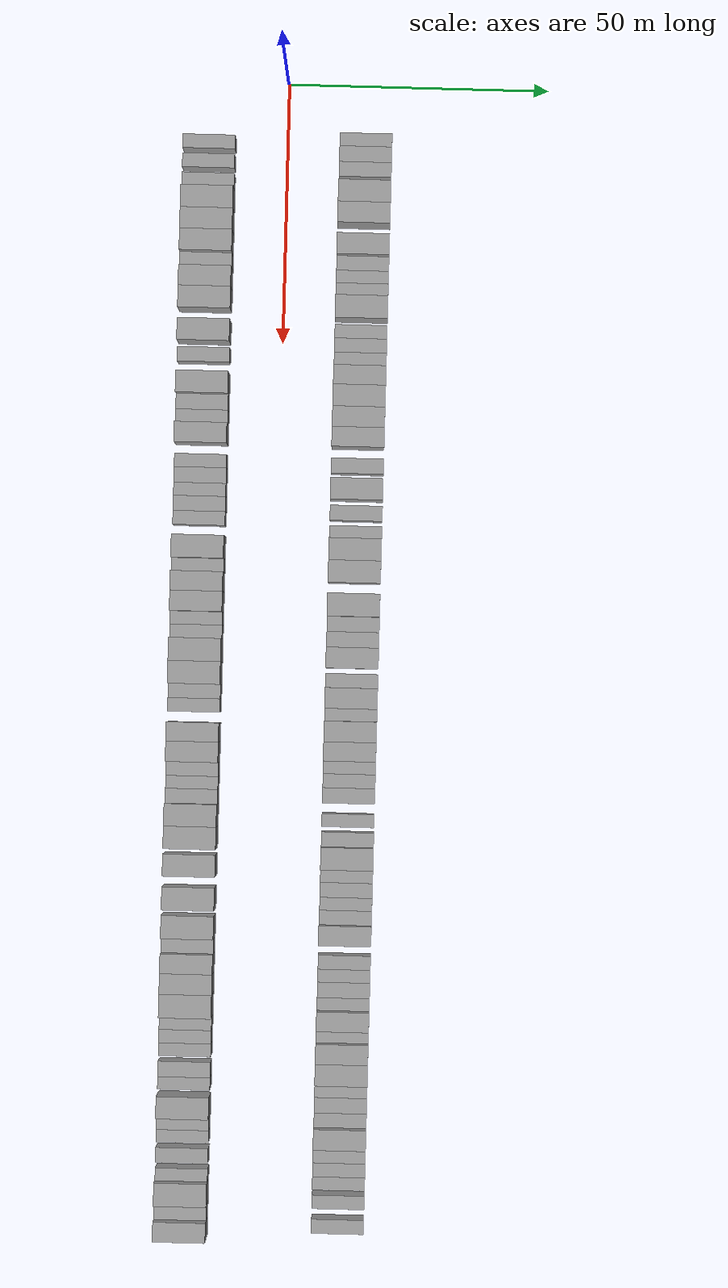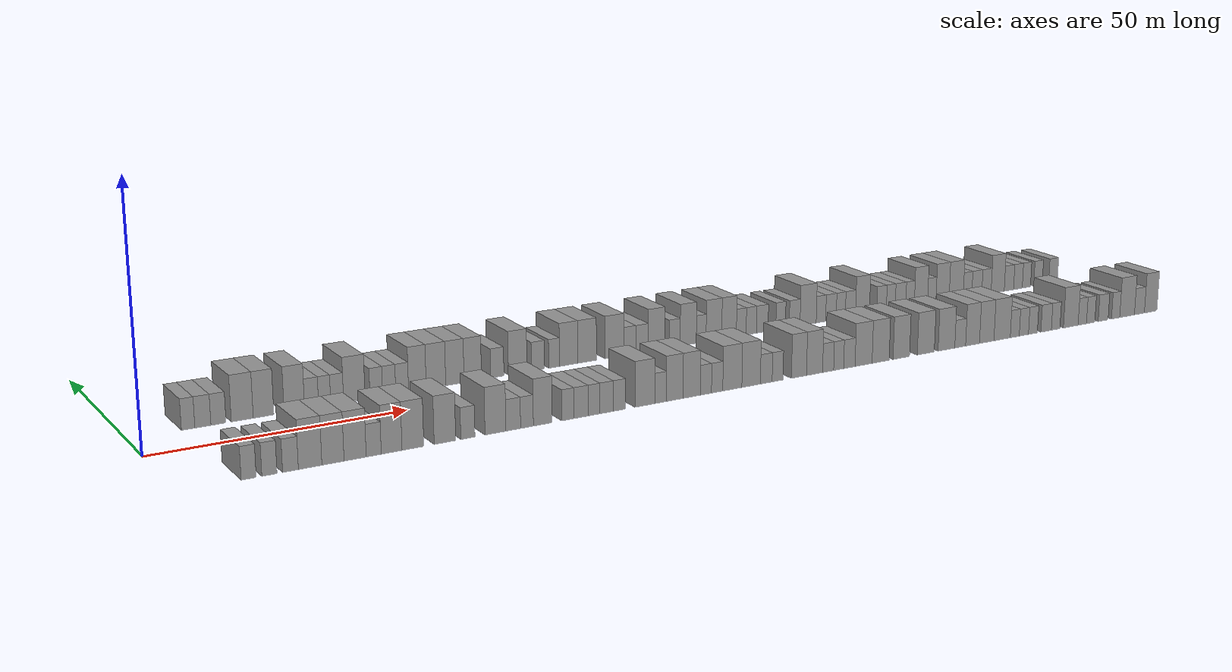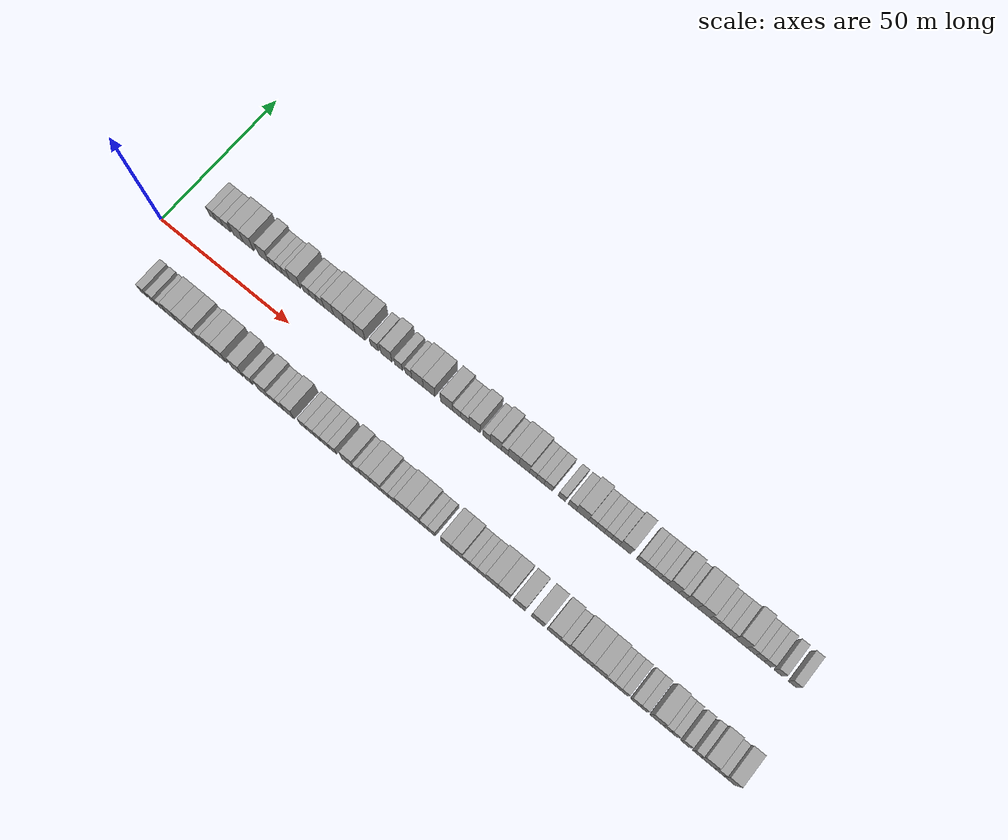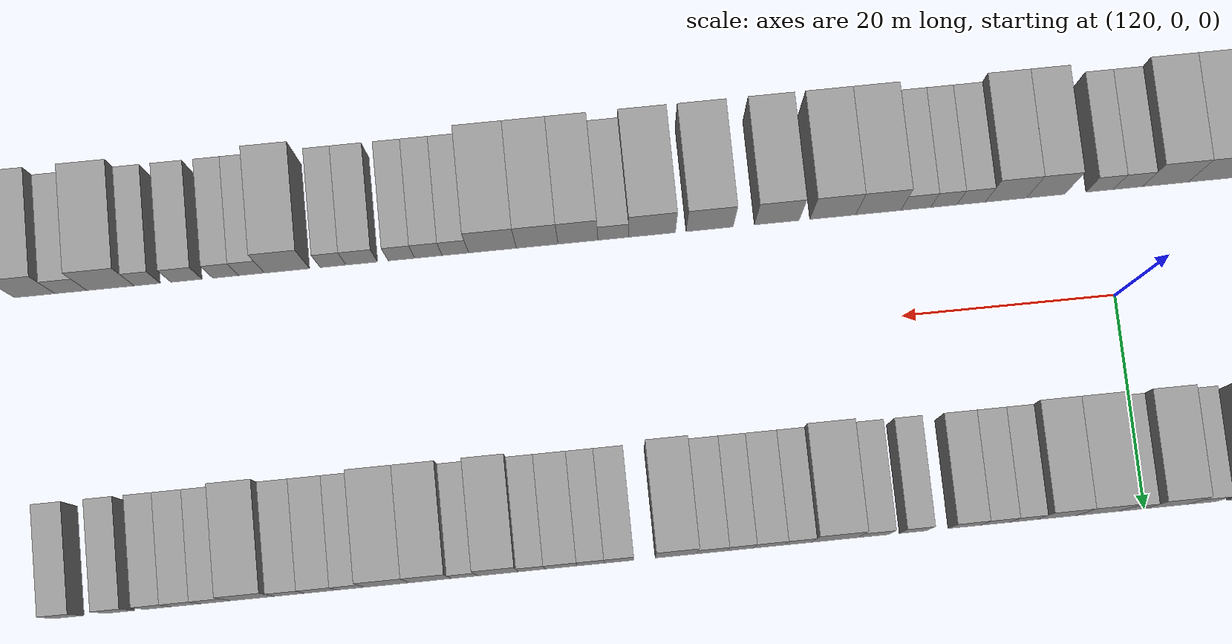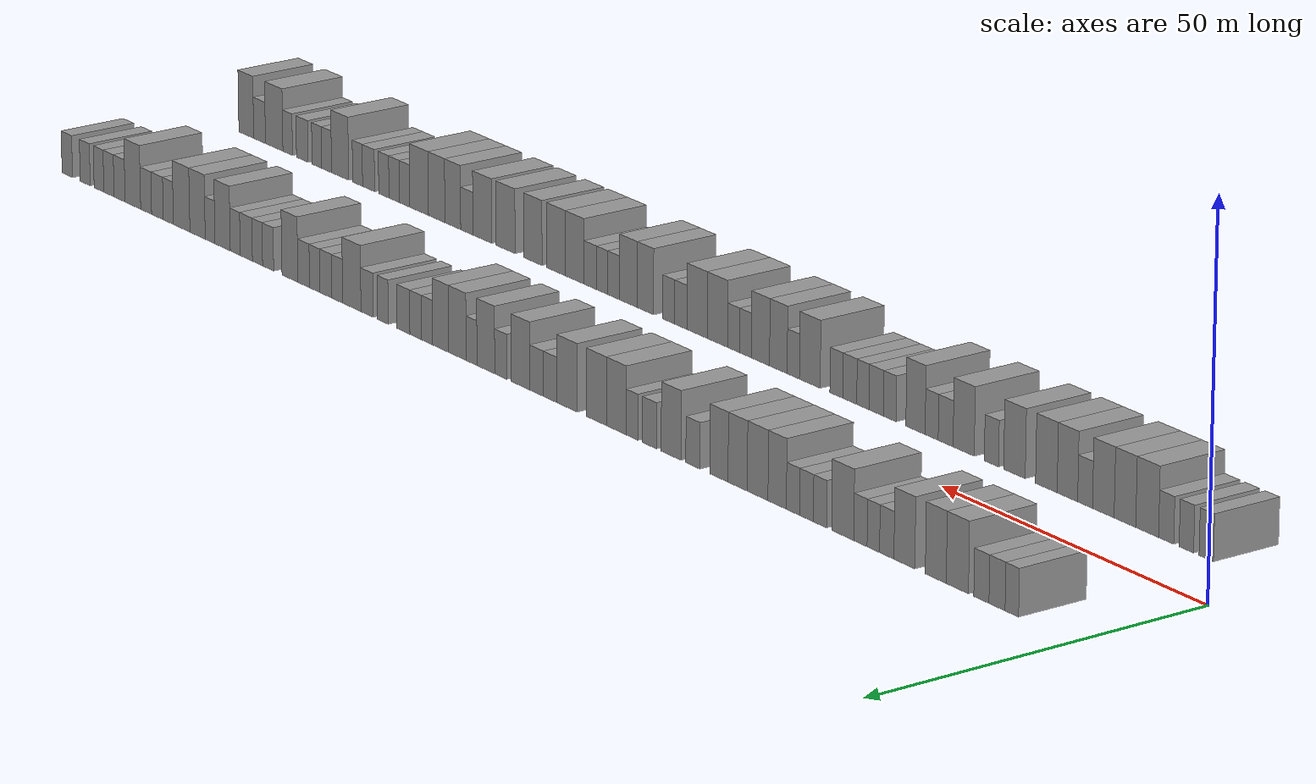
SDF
<sdf version="1.6">
 <world name="default">
  <scene>
   <sky><clouds><speed>12</speed></clouds></sky>
   <ambient>0.4 0.4 0.4 1</ambient>
   <background>0.7 0.7 0.7 1</background>
   <shadows>1</shadows>
  </scene>
  <gravity>0 0 -9.8066</gravity>
  <magnetic_field>6e-06 2.3e-05 -4.2e-05</magnetic_field>
  <physics default="0" name="default_physics" type="ode">
   <ode>
    <solver>
     <type>quick</type>
     <iters>10</iters>
     <sor>1.0</sor>
     <use_dynamic_moi_rescaling>0</use_dynamic_moi_rescaling>
    </solver>
    <constraints>
     <cfm>0</cfm>
     <erp>0.2</erp>
     <contact_max_correcting_vel>100</contact_max_correcting_vel>
     <contact_surface_layer>0.001</contact_surface_layer>
    </constraints>
   </ode>
   <max_step_size>0.004</max_step_size>
   <real_time_factor>1</real_time_factor>
   <real_time_update_rate>250</real_time_update_rate>
  </physics>
  <light name="sun" type="directional">
   <pose>0 0 10 0 0 0</pose>
   <diffuse>0.8 0.8 0.8 1</diffuse>
   <specular>0.2 0.2 0.2 1</specular>
   <attenuation>
    <range>1000</range>
    <constant>0.9</constant>
    <linear>0.01</linear>
    <quadratic>0.001</quadratic>
   </attenuation>
   <direction>-0.5 0.1 -0.9</direction>
  </light>
  <model name="building_1">
   <static>1</static>
   <pose>11.2514 15.0000 0 0.000000 0.000000 1.570796</pose>
   <link name="link">
    <pose>0 0 3.00 0 0 0</pose>
    <collision name="collision"><geometry><box><size>10.0000 2.5029 6.0000</size></box></geometry></collision>
    <visual name="visual">
     <cast_shadows>0</cast_shadows>
     <geometry><box><size>10.0000 2.5029 6.0000</size></box></geometry>
     <material>
      <script>
       <uri>model://grey_wall/materials/scripts</uri>
       <uri>model://grey_wall/materials/textures</uri>
       <name>vrc/grey_wall</name>
      </script>
     </material>
    </visual>
   </link>
  </model>
  <model name="building_2">
   <static>1</static>
   <pose>14.0023 15.0000 0 0.000000 0.000000 1.570796</pose>
   <link name="link">
    <pose>0 0 3.00 0 0 0</pose>
    <collision name="collision"><geometry><box><size>10.0000 2.9989 6.0000</size></box></geometry></collision>
    <visual name="visual">
     <cast_shadows>0</cast_shadows>
     <geometry><box><size>10.0000 2.9989 6.0000</size></box></geometry>
     <material>
      <script>
       <uri>model://grey_wall/materials/scripts</uri>
       <uri>model://grey_wall/materials/textures</uri>
       <name>vrc/grey_wall</name>
      </script>
     </material>
    </visual>
   </link>
  </model>
  <model name="building_3">
   <static>1</static>
   <pose>16.9239 15.0000 0 0.000000 0.000000 1.570796</pose>
   <link name="link">
    <pose>0 0 3.00 0 0 0</pose>
    <collision name="collision"><geometry><box><size>10.0000 2.8441 6.0000</size></box></geometry></collision>
    <visual name="visual">
     <cast_shadows>0</cast_shadows>
     <geometry><box><size>10.0000 2.8441 6.0000</size></box></geometry>
     <material>
      <script>
       <uri>model://grey_wall/materials/scripts</uri>
       <uri>model://grey_wall/materials/textures</uri>
       <name>vrc/grey_wall</name>
      </script>
     </material>
    </visual>
   </link>
  </model>
  <model name="building_4">
   <static>1</static>
   <pose>21.4435 15.0000 0 0.000000 0.000000 1.570796</pose>
   <link name="link">
    <pose>0 0 4.50 0 0 0</pose>
    <collision name="collision"><geometry><box><size>10.0000 4.1951 9.0000</size></box></geometry></collision>
    <visual name="visual">
     <cast_shadows>0</cast_shadows>
     <geometry><box><size>10.0000 4.1951 9.0000</size></box></geometry>
     <material>
      <script>
       <uri>model://grey_wall/materials/scripts</uri>
       <uri>model://grey_wall/materials/textures</uri>
       <name>vrc/grey_wall</name>
      </script>
     </material>
    </visual>
   </link>
  </model>
  <model name="building_5">
   <static>1</static>
   <pose>25.5285 15.0000 0 0.000000 0.000000 1.570796</pose>
   <link name="link">
    <pose>0 0 4.50 0 0 0</pose>
    <collision name="collision"><geometry><box><size>10.0000 3.9750 9.0000</size></box></geometry></collision>
    <visual name="visual">
     <cast_shadows>0</cast_shadows>
     <geometry><box><size>10.0000 3.9750 9.0000</size></box></geometry>
     <material>
      <script>
       <uri>model://grey_wall/materials/scripts</uri>
       <uri>model://grey_wall/materials/textures</uri>
       <name>vrc/grey_wall</name>
      </script>
     </material>
    </visual>
   </link>
  </model>
  <model name="building_6">
   <static>1</static>
   <pose>31.5260 15.0000 0 0.000000 0.000000 1.570796</pose>
   <link name="link">
    <pose>0 0 4.50 0 0 0</pose>
    <collision name="collision"><geometry><box><size>10.0000 4.0201 9.0000</size></box></geometry></collision>
    <visual name="visual">
     <cast_shadows>0</cast_shadows>
     <geometry><box><size>10.0000 4.0201 9.0000</size></box></geometry>
     <material>
      <script>
       <uri>model://grey_wall/materials/scripts</uri>
       <uri>model://grey_wall/materials/textures</uri>
       <name>vrc/grey_wall</name>
      </script>
     </material>
    </visual>
   </link>
  </model>
  <model name="building_7">
   <static>1</static>
   <pose>34.9230 15.0000 0 0.000000 0.000000 1.570796</pose>
   <link name="link">
    <pose>0 0 3.00 0 0 0</pose>
    <collision name="collision"><geometry><box><size>10.0000 2.7737 6.0000</size></box></geometry></collision>
    <visual name="visual">
     <cast_shadows>0</cast_shadows>
     <geometry><box><size>10.0000 2.7737 6.0000</size></box></geometry>
     <material>
      <script>
       <uri>model://grey_wall/materials/scripts</uri>
       <uri>model://grey_wall/materials/textures</uri>
       <name>vrc/grey_wall</name>
      </script>
     </material>
    </visual>
   </link>
  </model>
  <model name="building_8">
   <static>1</static>
   <pose>37.5219 15.0000 0 0.000000 0.000000 1.570796</pose>
   <link name="link">
    <pose>0 0 3.00 0 0 0</pose>
    <collision name="collision"><geometry><box><size>10.0000 2.4242 6.0000</size></box></geometry></collision>
    <visual name="visual">
     <cast_shadows>0</cast_shadows>
     <geometry><box><size>10.0000 2.4242 6.0000</size></box></geometry>
     <material>
      <script>
       <uri>model://grey_wall/materials/scripts</uri>
       <uri>model://grey_wall/materials/textures</uri>
       <name>vrc/grey_wall</name>
      </script>
     </material>
    </visual>
   </link>
  </model>
  <model name="building_9">
   <static>1</static>
   <pose>40.0258 15.0000 0 0.000000 0.000000 1.570796</pose>
   <link name="link">
    <pose>0 0 3.00 0 0 0</pose>
    <collision name="collision"><geometry><box><size>10.0000 2.5834 6.0000</size></box></geometry></collision>
    <visual name="visual">
     <cast_shadows>0</cast_shadows>
     <geometry><box><size>10.0000 2.5834 6.0000</size></box></geometry>
     <material>
      <script>
       <uri>model://grey_wall/materials/scripts</uri>
       <uri>model://grey_wall/materials/textures</uri>
       <name>vrc/grey_wall</name>
      </script>
     </material>
    </visual>
   </link>
  </model>
  <model name="building_10">
   <static>1</static>
   <pose>43.4983 15.0000 0 0.000000 0.000000 1.570796</pose>
   <link name="link">
    <pose>0 0 4.50 0 0 0</pose>
    <collision name="collision"><geometry><box><size>10.0000 4.3616 9.0000</size></box></geometry></collision>
    <visual name="visual">
     <cast_shadows>0</cast_shadows>
     <geometry><box><size>10.0000 4.3616 9.0000</size></box></geometry>
     <material>
      <script>
       <uri>model://grey_wall/materials/scripts</uri>
       <uri>model://grey_wall/materials/textures</uri>
       <name>vrc/grey_wall</name>
      </script>
     </material>
    </visual>
   </link>
  </model>
  <model name="building_11">
   <static>1</static>
   <pose>47.9770 15.0000 0 0.000000 0.000000 1.570796</pose>
   <link name="link">
    <pose>0 0 3.00 0 0 0</pose>
    <collision name="collision"><geometry><box><size>10.0000 2.5957 6.0000</size></box></geometry></collision>
    <visual name="visual">
     <cast_shadows>0</cast_shadows>
     <geometry><box><size>10.0000 2.5957 6.0000</size></box></geometry>
     <material>
      <script>
       <uri>model://grey_wall/materials/scripts</uri>
       <uri>model://grey_wall/materials/textures</uri>
       <name>vrc/grey_wall</name>
      </script>
     </material>
    </visual>
   </link>
  </model>
  <model name="building_12">
   <static>1</static>
   <pose>50.6294 15.0000 0 0.000000 0.000000 1.570796</pose>
   <link name="link">
    <pose>0 0 3.00 0 0 0</pose>
    <collision name="collision"><geometry><box><size>10.0000 2.7092 6.0000</size></box></geometry></collision>
    <visual name="visual">
     <cast_shadows>0</cast_shadows>
     <geometry><box><size>10.0000 2.7092 6.0000</size></box></geometry>
     <material>
      <script>
       <uri>model://grey_wall/materials/scripts</uri>
       <uri>model://grey_wall/materials/textures</uri>
       <name>vrc/grey_wall</name>
      </script>
     </material>
    </visual>
   </link>
  </model>
  <model name="building_13">
   <static>1</static>
   <pose>53.3160 15.0000 0 0.000000 0.000000 1.570796</pose>
   <link name="link">
    <pose>0 0 3.00 0 0 0</pose>
    <collision name="collision"><geometry><box><size>10.0000 2.6641 6.0000</size></box></geometry></collision>
    <visual name="visual">
     <cast_shadows>0</cast_shadows>
     <geometry><box><size>10.0000 2.6641 6.0000</size></box></geometry>
     <material>
      <script>
       <uri>model://grey_wall/materials/scripts</uri>
       <uri>model://grey_wall/materials/textures</uri>
       <name>vrc/grey_wall</name>
      </script>
     </material>
    </visual>
   </link>
  </model>
  <model name="building_14">
   <static>1</static>
   <pose>56.5004 15.0000 0 0.000000 0.000000 1.570796</pose>
   <link name="link">
    <pose>0 0 4.50 0 0 0</pose>
    <collision name="collision"><geometry><box><size>10.0000 3.7046 9.0000</size></box></geometry></collision>
    <visual name="visual">
     <cast_shadows>0</cast_shadows>
     <geometry><box><size>10.0000 3.7046 9.0000</size></box></geometry>
     <material>
      <script>
       <uri>model://grey_wall/materials/scripts</uri>
       <uri>model://grey_wall/materials/textures</uri>
       <name>vrc/grey_wall</name>
      </script>
     </material>
    </visual>
   </link>
  </model>
  <model name="building_15">
   <static>1</static>
   <pose>60.4283 15.0000 0 0.000000 0.000000 1.570796</pose>
   <link name="link">
    <pose>0 0 4.50 0 0 0</pose>
    <collision name="collision"><geometry><box><size>10.0000 4.1512 9.0000</size></box></geometry></collision>
    <visual name="visual">
     <cast_shadows>0</cast_shadows>
     <geometry><box><size>10.0000 4.1512 9.0000</size></box></geometry>
     <material>
      <script>
       <uri>model://grey_wall/materials/scripts</uri>
       <uri>model://grey_wall/materials/textures</uri>
       <name>vrc/grey_wall</name>
      </script>
     </material>
    </visual>
   </link>
  </model>
  <model name="building_16">
   <static>1</static>
   <pose>64.4689 15.0000 0 0.000000 0.000000 1.570796</pose>
   <link name="link">
    <pose>0 0 4.50 0 0 0</pose>
    <collision name="collision"><geometry><box><size>10.0000 3.9300 9.0000</size></box></geometry></collision>
    <visual name="visual">
     <cast_shadows>0</cast_shadows>
     <geometry><box><size>10.0000 3.9300 9.0000</size></box></geometry>
     <material>
      <script>
       <uri>model://grey_wall/materials/scripts</uri>
       <uri>model://grey_wall/materials/textures</uri>
       <name>vrc/grey_wall</name>
      </script>
     </material>
    </visual>
   </link>
  </model>
  <model name="building_17">
   <static>1</static>
   <pose>68.3168 15.0000 0 0.000000 0.000000 1.570796</pose>
   <link name="link">
    <pose>0 0 4.50 0 0 0</pose>
    <collision name="collision"><geometry><box><size>10.0000 3.7660 9.0000</size></box></geometry></collision>
    <visual name="visual">
     <cast_shadows>0</cast_shadows>
     <geometry><box><size>10.0000 3.7660 9.0000</size></box></geometry>
     <material>
      <script>
       <uri>model://grey_wall/materials/scripts</uri>
       <uri>model://grey_wall/materials/textures</uri>
       <name>vrc/grey_wall</name>
      </script>
     </material>
    </visual>
   </link>
  </model>
  <model name="building_18">
   <static>1</static>
   <pose>73.6593 15.0000 0 0.000000 0.000000 1.570796</pose>
   <link name="link">
    <pose>0 0 3.00 0 0 0</pose>
    <collision name="collision"><geometry><box><size>10.0000 2.9189 6.0000</size></box></geometry></collision>
    <visual name="visual">
     <cast_shadows>0</cast_shadows>
     <geometry><box><size>10.0000 2.9189 6.0000</size></box></geometry>
     <material>
      <script>
       <uri>model://grey_wall/materials/scripts</uri>
       <uri>model://grey_wall/materials/textures</uri>
       <name>vrc/grey_wall</name>
      </script>
     </material>
    </visual>
   </link>
  </model>
  <model name="building_19">
   <static>1</static>
   <pose>78.1737 15.0000 0 0.000000 0.000000 1.570796</pose>
   <link name="link">
    <pose>0 0 4.50 0 0 0</pose>
    <collision name="collision"><geometry><box><size>10.0000 4.1099 9.0000</size></box></geometry></collision>
    <visual name="visual">
     <cast_shadows>0</cast_shadows>
     <geometry><box><size>10.0000 4.1099 9.0000</size></box></geometry>
     <material>
      <script>
       <uri>model://grey_wall/materials/scripts</uri>
       <uri>model://grey_wall/materials/textures</uri>
       <name>vrc/grey_wall</name>
      </script>
     </material>
    </visual>
   </link>
  </model>
  <model name="building_20">
   <static>1</static>
   <pose>82.6827 15.0000 0 0.000000 0.000000 1.570796</pose>
   <link name="link">
    <pose>0 0 3.00 0 0 0</pose>
    <collision name="collision"><geometry><box><size>10.0000 2.9082 6.0000</size></box></geometry></collision>
    <visual name="visual">
     <cast_shadows>0</cast_shadows>
     <geometry><box><size>10.0000 2.9082 6.0000</size></box></geometry>
     <material>
      <script>
       <uri>model://grey_wall/materials/scripts</uri>
       <uri>model://grey_wall/materials/textures</uri>
       <name>vrc/grey_wall</name>
      </script>
     </material>
    </visual>
   </link>
  </model>
  <model name="building_21">
   <static>1</static>
   <pose>86.3541 15.0000 0 0.000000 0.000000 1.570796</pose>
   <link name="link">
    <pose>0 0 3.00 0 0 0</pose>
    <collision name="collision"><geometry><box><size>10.0000 2.4345 6.0000</size></box></geometry></collision>
    <visual name="visual">
     <cast_shadows>0</cast_shadows>
     <geometry><box><size>10.0000 2.4345 6.0000</size></box></geometry>
     <material>
      <script>
       <uri>model://grey_wall/materials/scripts</uri>
       <uri>model://grey_wall/materials/textures</uri>
       <name>vrc/grey_wall</name>
      </script>
     </material>
    </visual>
   </link>
  </model>
  <model name="building_22">
   <static>1</static>
   <pose>89.6806 15.0000 0 0.000000 0.000000 1.570796</pose>
   <link name="link">
    <pose>0 0 4.50 0 0 0</pose>
    <collision name="collision"><geometry><box><size>10.0000 4.2186 9.0000</size></box></geometry></collision>
    <visual name="visual">
     <cast_shadows>0</cast_shadows>
     <geometry><box><size>10.0000 4.2186 9.0000</size></box></geometry>
     <material>
      <script>
       <uri>model://grey_wall/materials/scripts</uri>
       <uri>model://grey_wall/materials/textures</uri>
       <name>vrc/grey_wall</name>
      </script>
     </material>
    </visual>
   </link>
  </model>
  <model name="building_23">
   <static>1</static>
   <pose>93.9344 15.0000 0 0.000000 0.000000 1.570796</pose>
   <link name="link">
    <pose>0 0 4.50 0 0 0</pose>
    <collision name="collision"><geometry><box><size>10.0000 4.2889 9.0000</size></box></geometry></collision>
    <visual name="visual">
     <cast_shadows>0</cast_shadows>
     <geometry><box><size>10.0000 4.2889 9.0000</size></box></geometry>
     <material>
      <script>
       <uri>model://grey_wall/materials/scripts</uri>
       <uri>model://grey_wall/materials/textures</uri>
       <name>vrc/grey_wall</name>
      </script>
     </material>
    </visual>
   </link>
  </model>
  <model name="building_24">
   <static>1</static>
   <pose>100.2766 15.0000 0 0.000000 0.000000 1.570796</pose>
   <link name="link">
    <pose>0 0 4.50 0 0 0</pose>
    <collision name="collision"><geometry><box><size>10.0000 4.3954 9.0000</size></box></geometry></collision>
    <visual name="visual">
     <cast_shadows>0</cast_shadows>
     <geometry><box><size>10.0000 4.3954 9.0000</size></box></geometry>
     <material>
      <script>
       <uri>model://grey_wall/materials/scripts</uri>
       <uri>model://grey_wall/materials/textures</uri>
       <name>vrc/grey_wall</name>
      </script>
     </material>
    </visual>
   </link>
  </model>
  <model name="building_25">
   <static>1</static>
   <pose>103.9257 15.0000 0 0.000000 0.000000 1.570796</pose>
   <link name="link">
    <pose>0 0 3.00 0 0 0</pose>
    <collision name="collision"><geometry><box><size>10.0000 2.9029 6.0000</size></box></geometry></collision>
    <visual name="visual">
     <cast_shadows>0</cast_shadows>
     <geometry><box><size>10.0000 2.9029 6.0000</size></box></geometry>
     <material>
      <script>
       <uri>model://grey_wall/materials/scripts</uri>
       <uri>model://grey_wall/materials/textures</uri>
       <name>vrc/grey_wall</name>
      </script>
     </material>
    </visual>
   </link>
  </model>
  <model name="building_26">
   <static>1</static>
   <pose>106.8754 15.0000 0 0.000000 0.000000 1.570796</pose>
   <link name="link">
    <pose>0 0 3.00 0 0 0</pose>
    <collision name="collision"><geometry><box><size>10.0000 2.9966 6.0000</size></box></geometry></collision>
    <visual name="visual">
     <cast_shadows>0</cast_shadows>
     <geometry><box><size>10.0000 2.9966 6.0000</size></box></geometry>
     <material>
      <script>
       <uri>model://grey_wall/materials/scripts</uri>
       <uri>model://grey_wall/materials/textures</uri>
       <name>vrc/grey_wall</name>
      </script>
     </material>
    </visual>
   </link>
  </model>
  <model name="building_27">
   <static>1</static>
   <pose>110.3782 15.0000 0 0.000000 0.000000 1.570796</pose>
   <link name="link">
    <pose>0 0 4.50 0 0 0</pose>
    <collision name="collision"><geometry><box><size>10.0000 4.0090 9.0000</size></box></geometry></collision>
    <visual name="visual">
     <cast_shadows>0</cast_shadows>
     <geometry><box><size>10.0000 4.0090 9.0000</size></box></geometry>
     <material>
      <script>
       <uri>model://grey_wall/materials/scripts</uri>
       <uri>model://grey_wall/materials/textures</uri>
       <name>vrc/grey_wall</name>
      </script>
     </material>
    </visual>
   </link>
  </model>
  <model name="building_28">
   <static>1</static>
   <pose>114.7304 15.0000 0 0.000000 0.000000 1.570796</pose>
   <link name="link">
    <pose>0 0 3.00 0 0 0</pose>
    <collision name="collision"><geometry><box><size>10.0000 2.6954 6.0000</size></box></geometry></collision>
    <visual name="visual">
     <cast_shadows>0</cast_shadows>
     <geometry><box><size>10.0000 2.6954 6.0000</size></box></geometry>
     <material>
      <script>
       <uri>model://grey_wall/materials/scripts</uri>
       <uri>model://grey_wall/materials/textures</uri>
       <name>vrc/grey_wall</name>
      </script>
     </material>
    </visual>
   </link>
  </model>
  <model name="building_29">
   <static>1</static>
   <pose>118.0491 15.0000 0 0.000000 0.000000 1.570796</pose>
   <link name="link">
    <pose>0 0 4.50 0 0 0</pose>
    <collision name="collision"><geometry><box><size>10.0000 3.9418 9.0000</size></box></geometry></collision>
    <visual name="visual">
     <cast_shadows>0</cast_shadows>
     <geometry><box><size>10.0000 3.9418 9.0000</size></box></geometry>
     <material>
      <script>
       <uri>model://grey_wall/materials/scripts</uri>
       <uri>model://grey_wall/materials/textures</uri>
       <name>vrc/grey_wall</name>
      </script>
     </material>
    </visual>
   </link>
  </model>
  <model name="building_30">
   <static>1</static>
   <pose>121.2317 15.0000 0 0.000000 0.000000 1.570796</pose>
   <link name="link">
    <pose>0 0 3.00 0 0 0</pose>
    <collision name="collision"><geometry><box><size>10.0000 2.4235 6.0000</size></box></geometry></collision>
    <visual name="visual">
     <cast_shadows>0</cast_shadows>
     <geometry><box><size>10.0000 2.4235 6.0000</size></box></geometry>
     <material>
      <script>
       <uri>model://grey_wall/materials/scripts</uri>
       <uri>model://grey_wall/materials/textures</uri>
       <name>vrc/grey_wall</name>
      </script>
     </material>
    </visual>
   </link>
  </model>
  <model name="building_31">
   <static>1</static>
   <pose>124.4070 15.0000 0 0.000000 0.000000 1.570796</pose>
   <link name="link">
    <pose>0 0 4.50 0 0 0</pose>
    <collision name="collision"><geometry><box><size>10.0000 3.9272 9.0000</size></box></geometry></collision>
    <visual name="visual">
     <cast_shadows>0</cast_shadows>
     <geometry><box><size>10.0000 3.9272 9.0000</size></box></geometry>
     <material>
      <script>
       <uri>model://grey_wall/materials/scripts</uri>
       <uri>model://grey_wall/materials/textures</uri>
       <name>vrc/grey_wall</name>
      </script>
     </material>
    </visual>
   </link>
  </model>
  <model name="building_32">
   <static>1</static>
   <pose>128.2069 15.0000 0 0.000000 0.000000 1.570796</pose>
   <link name="link">
    <pose>0 0 4.50 0 0 0</pose>
    <collision name="collision"><geometry><box><size>10.0000 3.6725 9.0000</size></box></geometry></collision>
    <visual name="visual">
     <cast_shadows>0</cast_shadows>
     <geometry><box><size>10.0000 3.6725 9.0000</size></box></geometry>
     <material>
      <script>
       <uri>model://grey_wall/materials/scripts</uri>
       <uri>model://grey_wall/materials/textures</uri>
       <name>vrc/grey_wall</name>
      </script>
     </material>
    </visual>
   </link>
  </model>
  <model name="building_33">
   <static>1</static>
   <pose>131.2854 15.0000 0 0.000000 0.000000 1.570796</pose>
   <link name="link">
    <pose>0 0 3.00 0 0 0</pose>
    <collision name="collision"><geometry><box><size>10.0000 2.4846 6.0000</size></box></geometry></collision>
    <visual name="visual">
     <cast_shadows>0</cast_shadows>
     <geometry><box><size>10.0000 2.4846 6.0000</size></box></geometry>
     <material>
      <script>
       <uri>model://grey_wall/materials/scripts</uri>
       <uri>model://grey_wall/materials/textures</uri>
       <name>vrc/grey_wall</name>
      </script>
     </material>
    </visual>
   </link>
  </model>
  <model name="building_34">
   <static>1</static>
   <pose>133.8589 15.0000 0 0.000000 0.000000 1.570796</pose>
   <link name="link">
    <pose>0 0 3.00 0 0 0</pose>
    <collision name="collision"><geometry><box><size>10.0000 2.6624 6.0000</size></box></geometry></collision>
    <visual name="visual">
     <cast_shadows>0</cast_shadows>
     <geometry><box><size>10.0000 2.6624 6.0000</size></box></geometry>
     <material>
      <script>
       <uri>model://grey_wall/materials/scripts</uri>
       <uri>model://grey_wall/materials/textures</uri>
       <name>vrc/grey_wall</name>
      </script>
     </material>
    </visual>
   </link>
  </model>
  <model name="building_35">
   <static>1</static>
   <pose>136.6706 15.0000 0 0.000000 0.000000 1.570796</pose>
   <link name="link">
    <pose>0 0 3.00 0 0 0</pose>
    <collision name="collision"><geometry><box><size>10.0000 2.9610 6.0000</size></box></geometry></collision>
    <visual name="visual">
     <cast_shadows>0</cast_shadows>
     <geometry><box><size>10.0000 2.9610 6.0000</size></box></geometry>
     <material>
      <script>
       <uri>model://grey_wall/materials/scripts</uri>
       <uri>model://grey_wall/materials/textures</uri>
       <name>vrc/grey_wall</name>
      </script>
     </material>
    </visual>
   </link>
  </model>
  <model name="building_36">
   <static>1</static>
   <pose>141.4017 15.0000 0 0.000000 0.000000 1.570796</pose>
   <link name="link">
    <pose>0 0 3.00 0 0 0</pose>
    <collision name="collision"><geometry><box><size>10.0000 2.5013 6.0000</size></box></geometry></collision>
    <visual name="visual">
     <cast_shadows>0</cast_shadows>
     <geometry><box><size>10.0000 2.5013 6.0000</size></box></geometry>
     <material>
      <script>
       <uri>model://grey_wall/materials/scripts</uri>
       <uri>model://grey_wall/materials/textures</uri>
       <name>vrc/grey_wall</name>
      </script>
     </material>
    </visual>
   </link>
  </model>
  <model name="building_37">
   <static>1</static>
   <pose>145.0635 15.0000 0 0.000000 0.000000 1.570796</pose>
   <link name="link">
    <pose>0 0 3.00 0 0 0</pose>
    <collision name="collision"><geometry><box><size>10.0000 2.8221 6.0000</size></box></geometry></collision>
    <visual name="visual">
     <cast_shadows>0</cast_shadows>
     <geometry><box><size>10.0000 2.8221 6.0000</size></box></geometry>
     <material>
      <script>
       <uri>model://grey_wall/materials/scripts</uri>
       <uri>model://grey_wall/materials/textures</uri>
       <name>vrc/grey_wall</name>
      </script>
     </material>
    </visual>
   </link>
  </model>
  <model name="building_38">
   <static>1</static>
   <pose>148.6118 15.0000 0 0.000000 0.000000 1.570796</pose>
   <link name="link">
    <pose>0 0 4.50 0 0 0</pose>
    <collision name="collision"><geometry><box><size>10.0000 4.2746 9.0000</size></box></geometry></collision>
    <visual name="visual">
     <cast_shadows>0</cast_shadows>
     <geometry><box><size>10.0000 4.2746 9.0000</size></box></geometry>
     <material>
      <script>
       <uri>model://grey_wall/materials/scripts</uri>
       <uri>model://grey_wall/materials/textures</uri>
       <name>vrc/grey_wall</name>
      </script>
     </material>
    </visual>
   </link>
  </model>
  <model name="building_39">
   <static>1</static>
   <pose>152.0125 15.0000 0 0.000000 0.000000 1.570796</pose>
   <link name="link">
    <pose>0 0 3.00 0 0 0</pose>
    <collision name="collision"><geometry><box><size>10.0000 2.5269 6.0000</size></box></geometry></collision>
    <visual name="visual">
     <cast_shadows>0</cast_shadows>
     <geometry><box><size>10.0000 2.5269 6.0000</size></box></geometry>
     <material>
      <script>
       <uri>model://grey_wall/materials/scripts</uri>
       <uri>model://grey_wall/materials/textures</uri>
       <name>vrc/grey_wall</name>
      </script>
     </material>
    </visual>
   </link>
  </model>
  <model name="building_40">
   <static>1</static>
   <pose>154.6877 15.0000 0 0.000000 0.000000 1.570796</pose>
   <link name="link">
    <pose>0 0 3.00 0 0 0</pose>
    <collision name="collision"><geometry><box><size>10.0000 2.8236 6.0000</size></box></geometry></collision>
    <visual name="visual">
     <cast_shadows>0</cast_shadows>
     <geometry><box><size>10.0000 2.8236 6.0000</size></box></geometry>
     <material>
      <script>
       <uri>model://grey_wall/materials/scripts</uri>
       <uri>model://grey_wall/materials/textures</uri>
       <name>vrc/grey_wall</name>
      </script>
     </material>
    </visual>
   </link>
  </model>
  <model name="building_41">
   <static>1</static>
   <pose>157.3309 15.0000 0 0.000000 0.000000 1.570796</pose>
   <link name="link">
    <pose>0 0 3.00 0 0 0</pose>
    <collision name="collision"><geometry><box><size>10.0000 2.4628 6.0000</size></box></geometry></collision>
    <visual name="visual">
     <cast_shadows>0</cast_shadows>
     <geometry><box><size>10.0000 2.4628 6.0000</size></box></geometry>
     <material>
      <script>
       <uri>model://grey_wall/materials/scripts</uri>
       <uri>model://grey_wall/materials/textures</uri>
       <name>vrc/grey_wall</name>
      </script>
     </material>
    </visual>
   </link>
  </model>
  <model name="building_42">
   <static>1</static>
   <pose>159.9496 15.0000 0 0.000000 0.000000 1.570796</pose>
   <link name="link">
    <pose>0 0 3.00 0 0 0</pose>
    <collision name="collision"><geometry><box><size>10.0000 2.7746 6.0000</size></box></geometry></collision>
    <visual name="visual">
     <cast_shadows>0</cast_shadows>
     <geometry><box><size>10.0000 2.7746 6.0000</size></box></geometry>
     <material>
      <script>
       <uri>model://grey_wall/materials/scripts</uri>
       <uri>model://grey_wall/materials/textures</uri>
       <name>vrc/grey_wall</name>
      </script>
     </material>
    </visual>
   </link>
  </model>
  <model name="building_43">
   <static>1</static>
   <pose>163.2400 15.0000 0 0.000000 0.000000 1.570796</pose>
   <link name="link">
    <pose>0 0 4.50 0 0 0</pose>
    <collision name="collision"><geometry><box><size>10.0000 3.8061 9.0000</size></box></geometry></collision>
    <visual name="visual">
     <cast_shadows>0</cast_shadows>
     <geometry><box><size>10.0000 3.8061 9.0000</size></box></geometry>
     <material>
      <script>
       <uri>model://grey_wall/materials/scripts</uri>
       <uri>model://grey_wall/materials/textures</uri>
       <name>vrc/grey_wall</name>
      </script>
     </material>
    </visual>
   </link>
  </model>
  <model name="building_44">
   <static>1</static>
   <pose>168.4815 15.0000 0 0.000000 0.000000 1.570796</pose>
   <link name="link">
    <pose>0 0 3.00 0 0 0</pose>
    <collision name="collision"><geometry><box><size>10.0000 2.6769 6.0000</size></box></geometry></collision>
    <visual name="visual">
     <cast_shadows>0</cast_shadows>
     <geometry><box><size>10.0000 2.6769 6.0000</size></box></geometry>
     <material>
      <script>
       <uri>model://grey_wall/materials/scripts</uri>
       <uri>model://grey_wall/materials/textures</uri>
       <name>vrc/grey_wall</name>
      </script>
     </material>
    </visual>
   </link>
  </model>
  <model name="building_45">
   <static>1</static>
   <pose>171.0509 15.0000 0 0.000000 0.000000 1.570796</pose>
   <link name="link">
    <pose>0 0 3.00 0 0 0</pose>
    <collision name="collision"><geometry><box><size>10.0000 2.4620 6.0000</size></box></geometry></collision>
    <visual name="visual">
     <cast_shadows>0</cast_shadows>
     <geometry><box><size>10.0000 2.4620 6.0000</size></box></geometry>
     <material>
      <script>
       <uri>model://grey_wall/materials/scripts</uri>
       <uri>model://grey_wall/materials/textures</uri>
       <name>vrc/grey_wall</name>
      </script>
     </material>
    </visual>
   </link>
  </model>
  <model name="building_46">
   <static>1</static>
   <pose>173.7625 15.0000 0 0.000000 0.000000 1.570796</pose>
   <link name="link">
    <pose>0 0 3.00 0 0 0</pose>
    <collision name="collision"><geometry><box><size>10.0000 2.9611 6.0000</size></box></geometry></collision>
    <visual name="visual">
     <cast_shadows>0</cast_shadows>
     <geometry><box><size>10.0000 2.9611 6.0000</size></box></geometry>
     <material>
      <script>
       <uri>model://grey_wall/materials/scripts</uri>
       <uri>model://grey_wall/materials/textures</uri>
       <name>vrc/grey_wall</name>
      </script>
     </material>
    </visual>
   </link>
  </model>
  <model name="building_47">
   <static>1</static>
   <pose>176.4523 15.0000 0 0.000000 0.000000 1.570796</pose>
   <link name="link">
    <pose>0 0 3.00 0 0 0</pose>
    <collision name="collision"><geometry><box><size>10.0000 2.4186 6.0000</size></box></geometry></collision>
    <visual name="visual">
     <cast_shadows>0</cast_shadows>
     <geometry><box><size>10.0000 2.4186 6.0000</size></box></geometry>
     <material>
      <script>
       <uri>model://grey_wall/materials/scripts</uri>
       <uri>model://grey_wall/materials/textures</uri>
       <name>vrc/grey_wall</name>
      </script>
     </material>
    </visual>
   </link>
  </model>
  <model name="building_48">
   <static>1</static>
   <pose>179.5392 15.0000 0 0.000000 0.000000 1.570796</pose>
   <link name="link">
    <pose>0 0 4.50 0 0 0</pose>
    <collision name="collision"><geometry><box><size>10.0000 3.7551 9.0000</size></box></geometry></collision>
    <visual name="visual">
     <cast_shadows>0</cast_shadows>
     <geometry><box><size>10.0000 3.7551 9.0000</size></box></geometry>
     <material>
      <script>
       <uri>model://grey_wall/materials/scripts</uri>
       <uri>model://grey_wall/materials/textures</uri>
       <name>vrc/grey_wall</name>
      </script>
     </material>
    </visual>
   </link>
  </model>
  <model name="building_49">
   <static>1</static>
   <pose>182.6211 15.0000 0 0.000000 0.000000 1.570796</pose>
   <link name="link">
    <pose>0 0 3.00 0 0 0</pose>
    <collision name="collision"><geometry><box><size>10.0000 2.4088 6.0000</size></box></geometry></collision>
    <visual name="visual">
     <cast_shadows>0</cast_shadows>
     <geometry><box><size>10.0000 2.4088 6.0000</size></box></geometry>
     <material>
      <script>
       <uri>model://grey_wall/materials/scripts</uri>
       <uri>model://grey_wall/materials/textures</uri>
       <name>vrc/grey_wall</name>
      </script>
     </material>
    </visual>
   </link>
  </model>
  <model name="building_50">
   <static>1</static>
   <pose>185.7264 15.0000 0 0.000000 0.000000 1.570796</pose>
   <link name="link">
    <pose>0 0 4.50 0 0 0</pose>
    <collision name="collision"><geometry><box><size>10.0000 3.8017 9.0000</size></box></geometry></collision>
    <visual name="visual">
     <cast_shadows>0</cast_shadows>
     <geometry><box><size>10.0000 3.8017 9.0000</size></box></geometry>
     <material>
      <script>
       <uri>model://grey_wall/materials/scripts</uri>
       <uri>model://grey_wall/materials/textures</uri>
       <name>vrc/grey_wall</name>
      </script>
     </material>
    </visual>
   </link>
  </model>
  <model name="building_51">
   <static>1</static>
   <pose>189.6800 15.0000 0 0.000000 0.000000 1.570796</pose>
   <link name="link">
    <pose>0 0 4.50 0 0 0</pose>
    <collision name="collision"><geometry><box><size>10.0000 4.1055 9.0000</size></box></geometry></collision>
    <visual name="visual">
     <cast_shadows>0</cast_shadows>
     <geometry><box><size>10.0000 4.1055 9.0000</size></box></geometry>
     <material>
      <script>
       <uri>model://grey_wall/materials/scripts</uri>
       <uri>model://grey_wall/materials/textures</uri>
       <name>vrc/grey_wall</name>
      </script>
     </material>
    </visual>
   </link>
  </model>
  <model name="building_52">
   <static>1</static>
   <pose>192.9981 15.0000 0 0.000000 0.000000 1.570796</pose>
   <link name="link">
    <pose>0 0 3.00 0 0 0</pose>
    <collision name="collision"><geometry><box><size>10.0000 2.5307 6.0000</size></box></geometry></collision>
    <visual name="visual">
     <cast_shadows>0</cast_shadows>
     <geometry><box><size>10.0000 2.5307 6.0000</size></box></geometry>
     <material>
      <script>
       <uri>model://grey_wall/materials/scripts</uri>
       <uri>model://grey_wall/materials/textures</uri>
       <name>vrc/grey_wall</name>
      </script>
     </material>
    </visual>
   </link>
  </model>
  <model name="building_53">
   <static>1</static>
   <pose>195.7391 15.0000 0 0.000000 0.000000 1.570796</pose>
   <link name="link">
    <pose>0 0 3.00 0 0 0</pose>
    <collision name="collision"><geometry><box><size>10.0000 2.9514 6.0000</size></box></geometry></collision>
    <visual name="visual">
     <cast_shadows>0</cast_shadows>
     <geometry><box><size>10.0000 2.9514 6.0000</size></box></geometry>
     <material>
      <script>
       <uri>model://grey_wall/materials/scripts</uri>
       <uri>model://grey_wall/materials/textures</uri>
       <name>vrc/grey_wall</name>
      </script>
     </material>
    </visual>
   </link>
  </model>
  <model name="building_54">
   <static>1</static>
   <pose>198.5940 15.0000 0 0.000000 0.000000 1.570796</pose>
   <link name="link">
    <pose>0 0 3.00 0 0 0</pose>
    <collision name="collision"><geometry><box><size>10.0000 2.7584 6.0000</size></box></geometry></collision>
    <visual name="visual">
     <cast_shadows>0</cast_shadows>
     <geometry><box><size>10.0000 2.7584 6.0000</size></box></geometry>
     <material>
      <script>
       <uri>model://grey_wall/materials/scripts</uri>
       <uri>model://grey_wall/materials/textures</uri>
       <name>vrc/grey_wall</name>
      </script>
     </material>
    </visual>
   </link>
  </model>
  <model name="building_55">
   <static>1</static>
   <pose>201.9436 15.0000 0 0.000000 0.000000 1.570796</pose>
   <link name="link">
    <pose>0 0 4.50 0 0 0</pose>
    <collision name="collision"><geometry><box><size>10.0000 3.9408 9.0000</size></box></geometry></collision>
    <visual name="visual">
     <cast_shadows>0</cast_shadows>
     <geometry><box><size>10.0000 3.9408 9.0000</size></box></geometry>
     <material>
      <script>
       <uri>model://grey_wall/materials/scripts</uri>
       <uri>model://grey_wall/materials/textures</uri>
       <name>vrc/grey_wall</name>
      </script>
     </material>
    </visual>
   </link>
  </model>
  <model name="building_56">
   <static>1</static>
   <pose>205.3190 15.0000 0 0.000000 0.000000 1.570796</pose>
   <link name="link">
    <pose>0 0 3.00 0 0 0</pose>
    <collision name="collision"><geometry><box><size>10.0000 2.8100 6.0000</size></box></geometry></collision>
    <visual name="visual">
     <cast_shadows>0</cast_shadows>
     <geometry><box><size>10.0000 2.8100 6.0000</size></box></geometry>
     <material>
      <script>
       <uri>model://grey_wall/materials/scripts</uri>
       <uri>model://grey_wall/materials/textures</uri>
       <name>vrc/grey_wall</name>
      </script>
     </material>
    </visual>
   </link>
  </model>
  <model name="building_57">
   <static>1</static>
   <pose>208.0431 15.0000 0 0.000000 0.000000 1.570796</pose>
   <link name="link">
    <pose>0 0 3.00 0 0 0</pose>
    <collision name="collision"><geometry><box><size>10.0000 2.6382 6.0000</size></box></geometry></collision>
    <visual name="visual">
     <cast_shadows>0</cast_shadows>
     <geometry><box><size>10.0000 2.6382 6.0000</size></box></geometry>
     <material>
      <script>
       <uri>model://grey_wall/materials/scripts</uri>
       <uri>model://grey_wall/materials/textures</uri>
       <name>vrc/grey_wall</name>
      </script>
     </material>
    </visual>
   </link>
  </model>
  <model name="building_58">
   <static>1</static>
   <pose>210.6156 15.0000 0 0.000000 0.000000 1.570796</pose>
   <link name="link">
    <pose>0 0 3.00 0 0 0</pose>
    <collision name="collision"><geometry><box><size>10.0000 2.5069 6.0000</size></box></geometry></collision>
    <visual name="visual">
     <cast_shadows>0</cast_shadows>
     <geometry><box><size>10.0000 2.5069 6.0000</size></box></geometry>
     <material>
      <script>
       <uri>model://grey_wall/materials/scripts</uri>
       <uri>model://grey_wall/materials/textures</uri>
       <name>vrc/grey_wall</name>
      </script>
     </material>
    </visual>
   </link>
  </model>
  <model name="building_59">
   <static>1</static>
   <pose>214.1637 15.0000 0 0.000000 0.000000 1.570796</pose>
   <link name="link">
    <pose>0 0 3.00 0 0 0</pose>
    <collision name="collision"><geometry><box><size>10.0000 2.5893 6.0000</size></box></geometry></collision>
    <visual name="visual">
     <cast_shadows>0</cast_shadows>
     <geometry><box><size>10.0000 2.5893 6.0000</size></box></geometry>
     <material>
      <script>
       <uri>model://grey_wall/materials/scripts</uri>
       <uri>model://grey_wall/materials/textures</uri>
       <name>vrc/grey_wall</name>
      </script>
     </material>
    </visual>
   </link>
  </model>
  <model name="building_60">
   <static>1</static>
   <pose>218.8112 15.0000 0 0.000000 0.000000 1.570796</pose>
   <link name="link">
    <pose>0 0 3.00 0 0 0</pose>
    <collision name="collision"><geometry><box><size>10.0000 2.7057 6.0000</size></box></geometry></collision>
    <visual name="visual">
     <cast_shadows>0</cast_shadows>
     <geometry><box><size>10.0000 2.7057 6.0000</size></box></geometry>
     <material>
      <script>
       <uri>model://grey_wall/materials/scripts</uri>
       <uri>model://grey_wall/materials/textures</uri>
       <name>vrc/grey_wall</name>
      </script>
     </material>
    </visual>
   </link>
  </model>
  <model name="building_61">
   <static>1</static>
   <pose>12.3167 -15.0000 0 0.000000 0.000000 1.570796</pose>
   <link name="link">
    <pose>0 0 3.00 0 0 0</pose>
    <collision name="collision"><geometry><box><size>10.0000 2.6335 6.0000</size></box></geometry></collision>
    <visual name="visual">
     <cast_shadows>0</cast_shadows>
     <geometry><box><size>10.0000 2.6335 6.0000</size></box></geometry>
     <material>
      <script>
       <uri>model://grey_wall/materials/scripts</uri>
       <uri>model://grey_wall/materials/textures</uri>
       <name>vrc/grey_wall</name>
      </script>
     </material>
    </visual>
   </link>
  </model>
  <model name="building_62">
   <static>1</static>
   <pose>15.9717 -15.0000 0 0.000000 0.000000 1.570796</pose>
   <link name="link">
    <pose>0 0 3.00 0 0 0</pose>
    <collision name="collision"><geometry><box><size>10.0000 2.6764 6.0000</size></box></geometry></collision>
    <visual name="visual">
     <cast_shadows>0</cast_shadows>
     <geometry><box><size>10.0000 2.6764 6.0000</size></box></geometry>
     <material>
      <script>
       <uri>model://grey_wall/materials/scripts</uri>
       <uri>model://grey_wall/materials/textures</uri>
       <name>vrc/grey_wall</name>
      </script>
     </material>
    </visual>
   </link>
  </model>
  <model name="building_63">
   <static>1</static>
   <pose>19.7191 -15.0000 0 0.000000 0.000000 1.570796</pose>
   <link name="link">
    <pose>0 0 3.00 0 0 0</pose>
    <collision name="collision"><geometry><box><size>10.0000 2.8184 6.0000</size></box></geometry></collision>
    <visual name="visual">
     <cast_shadows>0</cast_shadows>
     <geometry><box><size>10.0000 2.8184 6.0000</size></box></geometry>
     <material>
      <script>
       <uri>model://grey_wall/materials/scripts</uri>
       <uri>model://grey_wall/materials/textures</uri>
       <name>vrc/grey_wall</name>
      </script>
     </material>
    </visual>
   </link>
  </model>
  <model name="building_64">
   <static>1</static>
   <pose>23.2573 -15.0000 0 0.000000 0.000000 1.570796</pose>
   <link name="link">
    <pose>0 0 4.50 0 0 0</pose>
    <collision name="collision"><geometry><box><size>10.0000 4.2580 9.0000</size></box></geometry></collision>
    <visual name="visual">
     <cast_shadows>0</cast_shadows>
     <geometry><box><size>10.0000 4.2580 9.0000</size></box></geometry>
     <material>
      <script>
       <uri>model://grey_wall/materials/scripts</uri>
       <uri>model://grey_wall/materials/textures</uri>
       <name>vrc/grey_wall</name>
      </script>
     </material>
    </visual>
   </link>
  </model>
  <model name="building_65">
   <static>1</static>
   <pose>27.4177 -15.0000 0 0.000000 0.000000 1.570796</pose>
   <link name="link">
    <pose>0 0 4.50 0 0 0</pose>
    <collision name="collision"><geometry><box><size>10.0000 4.0628 9.0000</size></box></geometry></collision>
    <visual name="visual">
     <cast_shadows>0</cast_shadows>
     <geometry><box><size>10.0000 4.0628 9.0000</size></box></geometry>
     <material>
      <script>
       <uri>model://grey_wall/materials/scripts</uri>
       <uri>model://grey_wall/materials/textures</uri>
       <name>vrc/grey_wall</name>
      </script>
     </material>
    </visual>
   </link>
  </model>
  <model name="building_66">
   <static>1</static>
   <pose>31.5006 -15.0000 0 0.000000 0.000000 1.570796</pose>
   <link name="link">
    <pose>0 0 4.50 0 0 0</pose>
    <collision name="collision"><geometry><box><size>10.0000 4.1030 9.0000</size></box></geometry></collision>
    <visual name="visual">
     <cast_shadows>0</cast_shadows>
     <geometry><box><size>10.0000 4.1030 9.0000</size></box></geometry>
     <material>
      <script>
       <uri>model://grey_wall/materials/scripts</uri>
       <uri>model://grey_wall/materials/textures</uri>
       <name>vrc/grey_wall</name>
      </script>
     </material>
    </visual>
   </link>
  </model>
  <model name="building_67">
   <static>1</static>
   <pose>34.9630 -15.0000 0 0.000000 0.000000 1.570796</pose>
   <link name="link">
    <pose>0 0 3.00 0 0 0</pose>
    <collision name="collision"><geometry><box><size>10.0000 2.8217 6.0000</size></box></geometry></collision>
    <visual name="visual">
     <cast_shadows>0</cast_shadows>
     <geometry><box><size>10.0000 2.8217 6.0000</size></box></geometry>
     <material>
      <script>
       <uri>model://grey_wall/materials/scripts</uri>
       <uri>model://grey_wall/materials/textures</uri>
       <name>vrc/grey_wall</name>
      </script>
     </material>
    </visual>
   </link>
  </model>
  <model name="building_68">
   <static>1</static>
   <pose>38.3397 -15.0000 0 0.000000 0.000000 1.570796</pose>
   <link name="link">
    <pose>0 0 4.50 0 0 0</pose>
    <collision name="collision"><geometry><box><size>10.0000 3.9317 9.0000</size></box></geometry></collision>
    <visual name="visual">
     <cast_shadows>0</cast_shadows>
     <geometry><box><size>10.0000 3.9317 9.0000</size></box></geometry>
     <material>
      <script>
       <uri>model://grey_wall/materials/scripts</uri>
       <uri>model://grey_wall/materials/textures</uri>
       <name>vrc/grey_wall</name>
      </script>
     </material>
    </visual>
   </link>
  </model>
  <model name="building_69">
   <static>1</static>
   <pose>42.3876 -15.0000 0 0.000000 0.000000 1.570796</pose>
   <link name="link">
    <pose>0 0 4.50 0 0 0</pose>
    <collision name="collision"><geometry><box><size>10.0000 4.1641 9.0000</size></box></geometry></collision>
    <visual name="visual">
     <cast_shadows>0</cast_shadows>
     <geometry><box><size>10.0000 4.1641 9.0000</size></box></geometry>
     <material>
      <script>
       <uri>model://grey_wall/materials/scripts</uri>
       <uri>model://grey_wall/materials/textures</uri>
       <name>vrc/grey_wall</name>
      </script>
     </material>
    </visual>
   </link>
  </model>
  <model name="building_70">
   <static>1</static>
   <pose>48.5709 -15.0000 0 0.000000 0.000000 1.570796</pose>
   <link name="link">
    <pose>0 0 4.50 0 0 0</pose>
    <collision name="collision"><geometry><box><size>10.0000 4.2025 9.0000</size></box></geometry></collision>
    <visual name="visual">
     <cast_shadows>0</cast_shadows>
     <geometry><box><size>10.0000 4.2025 9.0000</size></box></geometry>
     <material>
      <script>
       <uri>model://grey_wall/materials/scripts</uri>
       <uri>model://grey_wall/materials/textures</uri>
       <name>vrc/grey_wall</name>
      </script>
     </material>
    </visual>
   </link>
  </model>
  <model name="building_71">
   <static>1</static>
   <pose>53.0681 -15.0000 0 0.000000 0.000000 1.570796</pose>
   <link name="link">
    <pose>0 0 3.00 0 0 0</pose>
    <collision name="collision"><geometry><box><size>10.0000 2.7918 6.0000</size></box></geometry></collision>
    <visual name="visual">
     <cast_shadows>0</cast_shadows>
     <geometry><box><size>10.0000 2.7918 6.0000</size></box></geometry>
     <material>
      <script>
       <uri>model://grey_wall/materials/scripts</uri>
       <uri>model://grey_wall/materials/textures</uri>
       <name>vrc/grey_wall</name>
      </script>
     </material>
    </visual>
   </link>
  </model>
  <model name="building_72">
   <static>1</static>
   <pose>58.5598 -15.0000 0 0.000000 0.000000 1.570796</pose>
   <link name="link">
    <pose>0 0 4.50 0 0 0</pose>
    <collision name="collision"><geometry><box><size>10.0000 4.1917 9.0000</size></box></geometry></collision>
    <visual name="visual">
     <cast_shadows>0</cast_shadows>
     <geometry><box><size>10.0000 4.1917 9.0000</size></box></geometry>
     <material>
      <script>
       <uri>model://grey_wall/materials/scripts</uri>
       <uri>model://grey_wall/materials/textures</uri>
       <name>vrc/grey_wall</name>
      </script>
     </material>
    </visual>
   </link>
  </model>
  <model name="building_73">
   <static>1</static>
   <pose>62.1411 -15.0000 0 0.000000 0.000000 1.570796</pose>
   <link name="link">
    <pose>0 0 3.00 0 0 0</pose>
    <collision name="collision"><geometry><box><size>10.0000 2.9708 6.0000</size></box></geometry></collision>
    <visual name="visual">
     <cast_shadows>0</cast_shadows>
     <geometry><box><size>10.0000 2.9708 6.0000</size></box></geometry>
     <material>
      <script>
       <uri>model://grey_wall/materials/scripts</uri>
       <uri>model://grey_wall/materials/textures</uri>
       <name>vrc/grey_wall</name>
      </script>
     </material>
    </visual>
   </link>
  </model>
  <model name="building_74">
   <static>1</static>
   <pose>64.9349 -15.0000 0 0.000000 0.000000 1.570796</pose>
   <link name="link">
    <pose>0 0 3.00 0 0 0</pose>
    <collision name="collision"><geometry><box><size>10.0000 2.6167 6.0000</size></box></geometry></collision>
    <visual name="visual">
     <cast_shadows>0</cast_shadows>
     <geometry><box><size>10.0000 2.6167 6.0000</size></box></geometry>
     <material>
      <script>
       <uri>model://grey_wall/materials/scripts</uri>
       <uri>model://grey_wall/materials/textures</uri>
       <name>vrc/grey_wall</name>
      </script>
     </material>
    </visual>
   </link>
  </model>
  <model name="building_75">
   <static>1</static>
   <pose>68.1829 -15.0000 0 0.000000 0.000000 1.570796</pose>
   <link name="link">
    <pose>0 0 4.50 0 0 0</pose>
    <collision name="collision"><geometry><box><size>10.0000 3.8792 9.0000</size></box></geometry></collision>
    <visual name="visual">
     <cast_shadows>0</cast_shadows>
     <geometry><box><size>10.0000 3.8792 9.0000</size></box></geometry>
     <material>
      <script>
       <uri>model://grey_wall/materials/scripts</uri>
       <uri>model://grey_wall/materials/textures</uri>
       <name>vrc/grey_wall</name>
      </script>
     </material>
    </visual>
   </link>
  </model>
  <model name="building_76">
   <static>1</static>
   <pose>73.3926 -15.0000 0 0.000000 0.000000 1.570796</pose>
   <link name="link">
    <pose>0 0 3.00 0 0 0</pose>
    <collision name="collision"><geometry><box><size>10.0000 2.5403 6.0000</size></box></geometry></collision>
    <visual name="visual">
     <cast_shadows>0</cast_shadows>
     <geometry><box><size>10.0000 2.5403 6.0000</size></box></geometry>
     <material>
      <script>
       <uri>model://grey_wall/materials/scripts</uri>
       <uri>model://grey_wall/materials/textures</uri>
       <name>vrc/grey_wall</name>
      </script>
     </material>
    </visual>
   </link>
  </model>
  <model name="building_77">
   <static>1</static>
   <pose>76.1578 -15.0000 0 0.000000 0.000000 1.570796</pose>
   <link name="link">
    <pose>0 0 3.00 0 0 0</pose>
    <collision name="collision"><geometry><box><size>10.0000 2.9901 6.0000</size></box></geometry></collision>
    <visual name="visual">
     <cast_shadows>0</cast_shadows>
     <geometry><box><size>10.0000 2.9901 6.0000</size></box></geometry>
     <material>
      <script>
       <uri>model://grey_wall/materials/scripts</uri>
       <uri>model://grey_wall/materials/textures</uri>
       <name>vrc/grey_wall</name>
      </script>
     </material>
    </visual>
   </link>
  </model>
  <model name="building_78">
   <static>1</static>
   <pose>78.8990 -15.0000 0 0.000000 0.000000 1.570796</pose>
   <link name="link">
    <pose>0 0 3.00 0 0 0</pose>
    <collision name="collision"><geometry><box><size>10.0000 2.4922 6.0000</size></box></geometry></collision>
    <visual name="visual">
     <cast_shadows>0</cast_shadows>
     <geometry><box><size>10.0000 2.4922 6.0000</size></box></geometry>
     <material>
      <script>
       <uri>model://grey_wall/materials/scripts</uri>
       <uri>model://grey_wall/materials/textures</uri>
       <name>vrc/grey_wall</name>
      </script>
     </material>
    </visual>
   </link>
  </model>
  <model name="building_79">
   <static>1</static>
   <pose>81.5900 -15.0000 0 0.000000 0.000000 1.570796</pose>
   <link name="link">
    <pose>0 0 3.00 0 0 0</pose>
    <collision name="collision"><geometry><box><size>10.0000 2.8898 6.0000</size></box></geometry></collision>
    <visual name="visual">
     <cast_shadows>0</cast_shadows>
     <geometry><box><size>10.0000 2.8898 6.0000</size></box></geometry>
     <material>
      <script>
       <uri>model://grey_wall/materials/scripts</uri>
       <uri>model://grey_wall/materials/textures</uri>
       <name>vrc/grey_wall</name>
      </script>
     </material>
    </visual>
   </link>
  </model>
  <model name="building_80">
   <static>1</static>
   <pose>84.3654 -15.0000 0 0.000000 0.000000 1.570796</pose>
   <link name="link">
    <pose>0 0 3.00 0 0 0</pose>
    <collision name="collision"><geometry><box><size>10.0000 2.6610 6.0000</size></box></geometry></collision>
    <visual name="visual">
     <cast_shadows>0</cast_shadows>
     <geometry><box><size>10.0000 2.6610 6.0000</size></box></geometry>
     <material>
      <script>
       <uri>model://grey_wall/materials/scripts</uri>
       <uri>model://grey_wall/materials/textures</uri>
       <name>vrc/grey_wall</name>
      </script>
     </material>
    </visual>
   </link>
  </model>
  <model name="building_81">
   <static>1</static>
   <pose>89.8745 -15.0000 0 0.000000 0.000000 1.570796</pose>
   <link name="link">
    <pose>0 0 4.50 0 0 0</pose>
    <collision name="collision"><geometry><box><size>10.0000 4.3572 9.0000</size></box></geometry></collision>
    <visual name="visual">
     <cast_shadows>0</cast_shadows>
     <geometry><box><size>10.0000 4.3572 9.0000</size></box></geometry>
     <material>
      <script>
       <uri>model://grey_wall/materials/scripts</uri>
       <uri>model://grey_wall/materials/textures</uri>
       <name>vrc/grey_wall</name>
      </script>
     </material>
    </visual>
   </link>
  </model>
  <model name="building_82">
   <static>1</static>
   <pose>93.3296 -15.0000 0 0.000000 0.000000 1.570796</pose>
   <link name="link">
    <pose>0 0 3.00 0 0 0</pose>
    <collision name="collision"><geometry><box><size>10.0000 2.5531 6.0000</size></box></geometry></collision>
    <visual name="visual">
     <cast_shadows>0</cast_shadows>
     <geometry><box><size>10.0000 2.5531 6.0000</size></box></geometry>
     <material>
      <script>
       <uri>model://grey_wall/materials/scripts</uri>
       <uri>model://grey_wall/materials/textures</uri>
       <name>vrc/grey_wall</name>
      </script>
     </material>
    </visual>
   </link>
  </model>
  <model name="building_83">
   <static>1</static>
   <pose>96.4717 -15.0000 0 0.000000 0.000000 1.570796</pose>
   <link name="link">
    <pose>0 0 4.50 0 0 0</pose>
    <collision name="collision"><geometry><box><size>10.0000 3.7310 9.0000</size></box></geometry></collision>
    <visual name="visual">
     <cast_shadows>0</cast_shadows>
     <geometry><box><size>10.0000 3.7310 9.0000</size></box></geometry>
     <material>
      <script>
       <uri>model://grey_wall/materials/scripts</uri>
       <uri>model://grey_wall/materials/textures</uri>
       <name>vrc/grey_wall</name>
      </script>
     </material>
    </visual>
   </link>
  </model>
  <model name="building_84">
   <static>1</static>
   <pose>100.2781 -15.0000 0 0.000000 0.000000 1.570796</pose>
   <link name="link">
    <pose>0 0 4.50 0 0 0</pose>
    <collision name="collision"><geometry><box><size>10.0000 3.8820 9.0000</size></box></geometry></collision>
    <visual name="visual">
     <cast_shadows>0</cast_shadows>
     <geometry><box><size>10.0000 3.8820 9.0000</size></box></geometry>
     <material>
      <script>
       <uri>model://grey_wall/materials/scripts</uri>
       <uri>model://grey_wall/materials/textures</uri>
       <name>vrc/grey_wall</name>
      </script>
     </material>
    </visual>
   </link>
  </model>
  <model name="building_85">
   <static>1</static>
   <pose>103.4728 -15.0000 0 0.000000 0.000000 1.570796</pose>
   <link name="link">
    <pose>0 0 3.00 0 0 0</pose>
    <collision name="collision"><geometry><box><size>10.0000 2.5074 6.0000</size></box></geometry></collision>
    <visual name="visual">
     <cast_shadows>0</cast_shadows>
     <geometry><box><size>10.0000 2.5074 6.0000</size></box></geometry>
     <material>
      <script>
       <uri>model://grey_wall/materials/scripts</uri>
       <uri>model://grey_wall/materials/textures</uri>
       <name>vrc/grey_wall</name>
      </script>
     </material>
    </visual>
   </link>
  </model>
  <model name="building_86">
   <static>1</static>
   <pose>106.0196 -15.0000 0 0.000000 0.000000 1.570796</pose>
   <link name="link">
    <pose>0 0 3.00 0 0 0</pose>
    <collision name="collision"><geometry><box><size>10.0000 2.5862 6.0000</size></box></geometry></collision>
    <visual name="visual">
     <cast_shadows>0</cast_shadows>
     <geometry><box><size>10.0000 2.5862 6.0000</size></box></geometry>
     <material>
      <script>
       <uri>model://grey_wall/materials/scripts</uri>
       <uri>model://grey_wall/materials/textures</uri>
       <name>vrc/grey_wall</name>
      </script>
     </material>
    </visual>
   </link>
  </model>
  <model name="building_87">
   <static>1</static>
   <pose>109.5107 -15.0000 0 0.000000 0.000000 1.570796</pose>
   <link name="link">
    <pose>0 0 4.50 0 0 0</pose>
    <collision name="collision"><geometry><box><size>10.0000 4.3960 9.0000</size></box></geometry></collision>
    <visual name="visual">
     <cast_shadows>0</cast_shadows>
     <geometry><box><size>10.0000 4.3960 9.0000</size></box></geometry>
     <material>
      <script>
       <uri>model://grey_wall/materials/scripts</uri>
       <uri>model://grey_wall/materials/textures</uri>
       <name>vrc/grey_wall</name>
      </script>
     </material>
    </visual>
   </link>
  </model>
  <model name="building_88">
   <static>1</static>
   <pose>113.8752 -15.0000 0 0.000000 0.000000 1.570796</pose>
   <link name="link">
    <pose>0 0 4.50 0 0 0</pose>
    <collision name="collision"><geometry><box><size>10.0000 4.3330 9.0000</size></box></geometry></collision>
    <visual name="visual">
     <cast_shadows>0</cast_shadows>
     <geometry><box><size>10.0000 4.3330 9.0000</size></box></geometry>
     <material>
      <script>
       <uri>model://grey_wall/materials/scripts</uri>
       <uri>model://grey_wall/materials/textures</uri>
       <name>vrc/grey_wall</name>
      </script>
     </material>
    </visual>
   </link>
  </model>
  <model name="building_89">
   <static>1</static>
   <pose>117.4212 -15.0000 0 0.000000 0.000000 1.570796</pose>
   <link name="link">
    <pose>0 0 3.00 0 0 0</pose>
    <collision name="collision"><geometry><box><size>10.0000 2.7589 6.0000</size></box></geometry></collision>
    <visual name="visual">
     <cast_shadows>0</cast_shadows>
     <geometry><box><size>10.0000 2.7589 6.0000</size></box></geometry>
     <material>
      <script>
       <uri>model://grey_wall/materials/scripts</uri>
       <uri>model://grey_wall/materials/textures</uri>
       <name>vrc/grey_wall</name>
      </script>
     </material>
    </visual>
   </link>
  </model>
  <model name="building_90">
   <static>1</static>
   <pose>120.0984 -15.0000 0 0.000000 0.000000 1.570796</pose>
   <link name="link">
    <pose>0 0 3.00 0 0 0</pose>
    <collision name="collision"><geometry><box><size>10.0000 2.5955 6.0000</size></box></geometry></collision>
    <visual name="visual">
     <cast_shadows>0</cast_shadows>
     <geometry><box><size>10.0000 2.5955 6.0000</size></box></geometry>
     <material>
      <script>
       <uri>model://grey_wall/materials/scripts</uri>
       <uri>model://grey_wall/materials/textures</uri>
       <name>vrc/grey_wall</name>
      </script>
     </material>
    </visual>
   </link>
  </model>
  <model name="building_91">
   <static>1</static>
   <pose>125.2078 -15.0000 0 0.000000 0.000000 1.570796</pose>
   <link name="link">
    <pose>0 0 4.50 0 0 0</pose>
    <collision name="collision"><geometry><box><size>10.0000 3.6233 9.0000</size></box></geometry></collision>
    <visual name="visual">
     <cast_shadows>0</cast_shadows>
     <geometry><box><size>10.0000 3.6233 9.0000</size></box></geometry>
     <material>
      <script>
       <uri>model://grey_wall/materials/scripts</uri>
       <uri>model://grey_wall/materials/textures</uri>
       <name>vrc/grey_wall</name>
      </script>
     </material>
    </visual>
   </link>
  </model>
  <model name="building_92">
   <static>1</static>
   <pose>128.9704 -15.0000 0 0.000000 0.000000 1.570796</pose>
   <link name="link">
    <pose>0 0 4.50 0 0 0</pose>
    <collision name="collision"><geometry><box><size>10.0000 3.9018 9.0000</size></box></geometry></collision>
    <visual name="visual">
     <cast_shadows>0</cast_shadows>
     <geometry><box><size>10.0000 3.9018 9.0000</size></box></geometry>
     <material>
      <script>
       <uri>model://grey_wall/materials/scripts</uri>
       <uri>model://grey_wall/materials/textures</uri>
       <name>vrc/grey_wall</name>
      </script>
     </material>
    </visual>
   </link>
  </model>
  <model name="building_93">
   <static>1</static>
   <pose>132.2763 -15.0000 0 0.000000 0.000000 1.570796</pose>
   <link name="link">
    <pose>0 0 3.00 0 0 0</pose>
    <collision name="collision"><geometry><box><size>10.0000 2.7100 6.0000</size></box></geometry></collision>
    <visual name="visual">
     <cast_shadows>0</cast_shadows>
     <geometry><box><size>10.0000 2.7100 6.0000</size></box></geometry>
     <material>
      <script>
       <uri>model://grey_wall/materials/scripts</uri>
       <uri>model://grey_wall/materials/textures</uri>
       <name>vrc/grey_wall</name>
      </script>
     </material>
    </visual>
   </link>
  </model>
  <model name="building_94">
   <static>1</static>
   <pose>134.8609 -15.0000 0 0.000000 0.000000 1.570796</pose>
   <link name="link">
    <pose>0 0 3.00 0 0 0</pose>
    <collision name="collision"><geometry><box><size>10.0000 2.4592 6.0000</size></box></geometry></collision>
    <visual name="visual">
     <cast_shadows>0</cast_shadows>
     <geometry><box><size>10.0000 2.4592 6.0000</size></box></geometry>
     <material>
      <script>
       <uri>model://grey_wall/materials/scripts</uri>
       <uri>model://grey_wall/materials/textures</uri>
       <name>vrc/grey_wall</name>
      </script>
     </material>
    </visual>
   </link>
  </model>
  <model name="building_95">
   <static>1</static>
   <pose>137.5062 -15.0000 0 0.000000 0.000000 1.570796</pose>
   <link name="link">
    <pose>0 0 3.00 0 0 0</pose>
    <collision name="collision"><geometry><box><size>10.0000 2.8316 6.0000</size></box></geometry></collision>
    <visual name="visual">
     <cast_shadows>0</cast_shadows>
     <geometry><box><size>10.0000 2.8316 6.0000</size></box></geometry>
     <material>
      <script>
       <uri>model://grey_wall/materials/scripts</uri>
       <uri>model://grey_wall/materials/textures</uri>
       <name>vrc/grey_wall</name>
      </script>
     </material>
    </visual>
   </link>
  </model>
  <model name="building_96">
   <static>1</static>
   <pose>141.0526 -15.0000 0 0.000000 0.000000 1.570796</pose>
   <link name="link">
    <pose>0 0 4.50 0 0 0</pose>
    <collision name="collision"><geometry><box><size>10.0000 4.2611 9.0000</size></box></geometry></collision>
    <visual name="visual">
     <cast_shadows>0</cast_shadows>
     <geometry><box><size>10.0000 4.2611 9.0000</size></box></geometry>
     <material>
      <script>
       <uri>model://grey_wall/materials/scripts</uri>
       <uri>model://grey_wall/materials/textures</uri>
       <name>vrc/grey_wall</name>
      </script>
     </material>
    </visual>
   </link>
  </model>
  <model name="building_97">
   <static>1</static>
   <pose>145.3453 -15.0000 0 0.000000 0.000000 1.570796</pose>
   <link name="link">
    <pose>0 0 4.50 0 0 0</pose>
    <collision name="collision"><geometry><box><size>10.0000 4.3242 9.0000</size></box></geometry></collision>
    <visual name="visual">
     <cast_shadows>0</cast_shadows>
     <geometry><box><size>10.0000 4.3242 9.0000</size></box></geometry>
     <material>
      <script>
       <uri>model://grey_wall/materials/scripts</uri>
       <uri>model://grey_wall/materials/textures</uri>
       <name>vrc/grey_wall</name>
      </script>
     </material>
    </visual>
   </link>
  </model>
  <model name="building_98">
   <static>1</static>
   <pose>150.6221 -15.0000 0 0.000000 0.000000 1.570796</pose>
   <link name="link">
    <pose>0 0 4.50 0 0 0</pose>
    <collision name="collision"><geometry><box><size>10.0000 4.2294 9.0000</size></box></geometry></collision>
    <visual name="visual">
     <cast_shadows>0</cast_shadows>
     <geometry><box><size>10.0000 4.2294 9.0000</size></box></geometry>
     <material>
      <script>
       <uri>model://grey_wall/materials/scripts</uri>
       <uri>model://grey_wall/materials/textures</uri>
       <name>vrc/grey_wall</name>
      </script>
     </material>
    </visual>
   </link>
  </model>
  <model name="building_99">
   <static>1</static>
   <pose>156.9536 -15.0000 0 0.000000 0.000000 1.570796</pose>
   <link name="link">
    <pose>0 0 4.50 0 0 0</pose>
    <collision name="collision"><geometry><box><size>10.0000 4.4337 9.0000</size></box></geometry></collision>
    <visual name="visual">
     <cast_shadows>0</cast_shadows>
     <geometry><box><size>10.0000 4.4337 9.0000</size></box></geometry>
     <material>
      <script>
       <uri>model://grey_wall/materials/scripts</uri>
       <uri>model://grey_wall/materials/textures</uri>
       <name>vrc/grey_wall</name>
      </script>
     </material>
    </visual>
   </link>
  </model>
  <model name="building_100">
   <static>1</static>
   <pose>162.3765 -15.0000 0 0.000000 0.000000 1.570796</pose>
   <link name="link">
    <pose>0 0 4.50 0 0 0</pose>
    <collision name="collision"><geometry><box><size>10.0000 4.4120 9.0000</size></box></geometry></collision>
    <visual name="visual">
     <cast_shadows>0</cast_shadows>
     <geometry><box><size>10.0000 4.4120 9.0000</size></box></geometry>
     <material>
      <script>
       <uri>model://grey_wall/materials/scripts</uri>
       <uri>model://grey_wall/materials/textures</uri>
       <name>vrc/grey_wall</name>
      </script>
     </material>
    </visual>
   </link>
  </model>
  <model name="building_101">
   <static>1</static>
   <pose>166.0239 -15.0000 0 0.000000 0.000000 1.570796</pose>
   <link name="link">
    <pose>0 0 3.00 0 0 0</pose>
    <collision name="collision"><geometry><box><size>10.0000 2.8829 6.0000</size></box></geometry></collision>
    <visual name="visual">
     <cast_shadows>0</cast_shadows>
     <geometry><box><size>10.0000 2.8829 6.0000</size></box></geometry>
     <material>
      <script>
       <uri>model://grey_wall/materials/scripts</uri>
       <uri>model://grey_wall/materials/textures</uri>
       <name>vrc/grey_wall</name>
      </script>
     </material>
    </visual>
   </link>
  </model>
  <model name="building_102">
   <static>1</static>
   <pose>169.3363 -15.0000 0 0.000000 0.000000 1.570796</pose>
   <link name="link">
    <pose>0 0 4.50 0 0 0</pose>
    <collision name="collision"><geometry><box><size>10.0000 3.7418 9.0000</size></box></geometry></collision>
    <visual name="visual">
     <cast_shadows>0</cast_shadows>
     <geometry><box><size>10.0000 3.7418 9.0000</size></box></geometry>
     <material>
      <script>
       <uri>model://grey_wall/materials/scripts</uri>
       <uri>model://grey_wall/materials/textures</uri>
       <name>vrc/grey_wall</name>
      </script>
     </material>
    </visual>
   </link>
  </model>
  <model name="building_103">
   <static>1</static>
   <pose>173.1660 -15.0000 0 0.000000 0.000000 1.570796</pose>
   <link name="link">
    <pose>0 0 4.50 0 0 0</pose>
    <collision name="collision"><geometry><box><size>10.0000 3.9175 9.0000</size></box></geometry></collision>
    <visual name="visual">
     <cast_shadows>0</cast_shadows>
     <geometry><box><size>10.0000 3.9175 9.0000</size></box></geometry>
     <material>
      <script>
       <uri>model://grey_wall/materials/scripts</uri>
       <uri>model://grey_wall/materials/textures</uri>
       <name>vrc/grey_wall</name>
      </script>
     </material>
    </visual>
   </link>
  </model>
  <model name="building_104">
   <static>1</static>
   <pose>177.3644 -15.0000 0 0.000000 0.000000 1.570796</pose>
   <link name="link">
    <pose>0 0 4.50 0 0 0</pose>
    <collision name="collision"><geometry><box><size>10.0000 4.4794 9.0000</size></box></geometry></collision>
    <visual name="visual">
     <cast_shadows>0</cast_shadows>
     <geometry><box><size>10.0000 4.4794 9.0000</size></box></geometry>
     <material>
      <script>
       <uri>model://grey_wall/materials/scripts</uri>
       <uri>model://grey_wall/materials/textures</uri>
       <name>vrc/grey_wall</name>
      </script>
     </material>
    </visual>
   </link>
  </model>
  <model name="building_105">
   <static>1</static>
   <pose>180.8478 -15.0000 0 0.000000 0.000000 1.570796</pose>
   <link name="link">
    <pose>0 0 3.00 0 0 0</pose>
    <collision name="collision"><geometry><box><size>10.0000 2.4873 6.0000</size></box></geometry></collision>
    <visual name="visual">
     <cast_shadows>0</cast_shadows>
     <geometry><box><size>10.0000 2.4873 6.0000</size></box></geometry>
     <material>
      <script>
       <uri>model://grey_wall/materials/scripts</uri>
       <uri>model://grey_wall/materials/textures</uri>
       <name>vrc/grey_wall</name>
      </script>
     </material>
    </visual>
   </link>
  </model>
  <model name="building_106">
   <static>1</static>
   <pose>183.3682 -15.0000 0 0.000000 0.000000 1.570796</pose>
   <link name="link">
    <pose>0 0 3.00 0 0 0</pose>
    <collision name="collision"><geometry><box><size>10.0000 2.5535 6.0000</size></box></geometry></collision>
    <visual name="visual">
     <cast_shadows>0</cast_shadows>
     <geometry><box><size>10.0000 2.5535 6.0000</size></box></geometry>
     <material>
      <script>
       <uri>model://grey_wall/materials/scripts</uri>
       <uri>model://grey_wall/materials/textures</uri>
       <name>vrc/grey_wall</name>
      </script>
     </material>
    </visual>
   </link>
  </model>
  <model name="building_107">
   <static>1</static>
   <pose>185.8934 -15.0000 0 0.000000 0.000000 1.570796</pose>
   <link name="link">
    <pose>0 0 3.00 0 0 0</pose>
    <collision name="collision"><geometry><box><size>10.0000 2.4969 6.0000</size></box></geometry></collision>
    <visual name="visual">
     <cast_shadows>0</cast_shadows>
     <geometry><box><size>10.0000 2.4969 6.0000</size></box></geometry>
     <material>
      <script>
       <uri>model://grey_wall/materials/scripts</uri>
       <uri>model://grey_wall/materials/textures</uri>
       <name>vrc/grey_wall</name>
      </script>
     </material>
    </visual>
   </link>
  </model>
  <model name="building_108">
   <static>1</static>
   <pose>189.6166 -15.0000 0 0.000000 0.000000 1.570796</pose>
   <link name="link">
    <pose>0 0 3.00 0 0 0</pose>
    <collision name="collision"><geometry><box><size>10.0000 2.9494 6.0000</size></box></geometry></collision>
    <visual name="visual">
     <cast_shadows>0</cast_shadows>
     <geometry><box><size>10.0000 2.9494 6.0000</size></box></geometry>
     <material>
      <script>
       <uri>model://grey_wall/materials/scripts</uri>
       <uri>model://grey_wall/materials/textures</uri>
       <name>vrc/grey_wall</name>
      </script>
     </material>
    </visual>
   </link>
  </model>
  <model name="building_109">
   <static>1</static>
   <pose>192.3065 -15.0000 0 0.000000 0.000000 1.570796</pose>
   <link name="link">
    <pose>0 0 3.00 0 0 0</pose>
    <collision name="collision"><geometry><box><size>10.0000 2.4305 6.0000</size></box></geometry></collision>
    <visual name="visual">
     <cast_shadows>0</cast_shadows>
     <geometry><box><size>10.0000 2.4305 6.0000</size></box></geometry>
     <material>
      <script>
       <uri>model://grey_wall/materials/scripts</uri>
       <uri>model://grey_wall/materials/textures</uri>
       <name>vrc/grey_wall</name>
      </script>
     </material>
    </visual>
   </link>
  </model>
  <model name="building_110">
   <static>1</static>
   <pose>196.6286 -15.0000 0 0.000000 0.000000 1.570796</pose>
   <link name="link">
    <pose>0 0 4.50 0 0 0</pose>
    <collision name="collision"><geometry><box><size>10.0000 4.2137 9.0000</size></box></geometry></collision>
    <visual name="visual">
     <cast_shadows>0</cast_shadows>
     <geometry><box><size>10.0000 4.2137 9.0000</size></box></geometry>
     <material>
      <script>
       <uri>model://grey_wall/materials/scripts</uri>
       <uri>model://grey_wall/materials/textures</uri>
       <name>vrc/grey_wall</name>
      </script>
     </material>
    </visual>
   </link>
  </model>
  <model name="building_111">
   <static>1</static>
   <pose>199.9498 -15.0000 0 0.000000 0.000000 1.570796</pose>
   <link name="link">
    <pose>0 0 3.00 0 0 0</pose>
    <collision name="collision"><geometry><box><size>10.0000 2.4287 6.0000</size></box></geometry></collision>
    <visual name="visual">
     <cast_shadows>0</cast_shadows>
     <geometry><box><size>10.0000 2.4287 6.0000</size></box></geometry>
     <material>
      <script>
       <uri>model://grey_wall/materials/scripts</uri>
       <uri>model://grey_wall/materials/textures</uri>
       <name>vrc/grey_wall</name>
      </script>
     </material>
    </visual>
   </link>
  </model>
  <model name="building_112">
   <static>1</static>
   <pose>202.3743 -15.0000 0 0.000000 0.000000 1.570796</pose>
   <link name="link">
    <pose>0 0 3.00 0 0 0</pose>
    <collision name="collision"><geometry><box><size>10.0000 2.4203 6.0000</size></box></geometry></collision>
    <visual name="visual">
     <cast_shadows>0</cast_shadows>
     <geometry><box><size>10.0000 2.4203 6.0000</size></box></geometry>
     <material>
      <script>
       <uri>model://grey_wall/materials/scripts</uri>
       <uri>model://grey_wall/materials/textures</uri>
       <name>vrc/grey_wall</name>
      </script>
     </material>
    </visual>
   </link>
  </model>
  <model name="building_113">
   <static>1</static>
   <pose>206.0370 -15.0000 0 0.000000 0.000000 1.570796</pose>
   <link name="link">
    <pose>0 0 3.00 0 0 0</pose>
    <collision name="collision"><geometry><box><size>10.0000 2.9051 6.0000</size></box></geometry></collision>
    <visual name="visual">
     <cast_shadows>0</cast_shadows>
     <geometry><box><size>10.0000 2.9051 6.0000</size></box></geometry>
     <material>
      <script>
       <uri>model://grey_wall/materials/scripts</uri>
       <uri>model://grey_wall/materials/textures</uri>
       <name>vrc/grey_wall</name>
      </script>
     </material>
    </visual>
   </link>
  </model>
  <model name="building_114">
   <static>1</static>
   <pose>209.7016 -15.0000 0 0.000000 0.000000 1.570796</pose>
   <link name="link">
    <pose>0 0 3.00 0 0 0</pose>
    <collision name="collision"><geometry><box><size>10.0000 2.4241 6.0000</size></box></geometry></collision>
    <visual name="visual">
     <cast_shadows>0</cast_shadows>
     <geometry><box><size>10.0000 2.4241 6.0000</size></box></geometry>
     <material>
      <script>
       <uri>model://grey_wall/materials/scripts</uri>
       <uri>model://grey_wall/materials/textures</uri>
       <name>vrc/grey_wall</name>
      </script>
     </material>
    </visual>
   </link>
  </model>
  <model name="building_115">
   <static>1</static>
   <pose>213.1197 -15.0000 0 0.000000 0.000000 1.570796</pose>
   <link name="link">
    <pose>0 0 4.50 0 0 0</pose>
    <collision name="collision"><geometry><box><size>10.0000 4.4122 9.0000</size></box></geometry></collision>
    <visual name="visual">
     <cast_shadows>0</cast_shadows>
     <geometry><box><size>10.0000 4.4122 9.0000</size></box></geometry>
     <material>
      <script>
       <uri>model://grey_wall/materials/scripts</uri>
       <uri>model://grey_wall/materials/textures</uri>
       <name>vrc/grey_wall</name>
      </script>
     </material>
    </visual>
   </link>
  </model>
  <model name="building_116">
   <static>1</static>
   <pose>216.8201 -15.0000 0 0.000000 0.000000 1.570796</pose>
   <link name="link">
    <pose>0 0 3.00 0 0 0</pose>
    <collision name="collision"><geometry><box><size>10.0000 2.9885 6.0000</size></box></geometry></collision>
    <visual name="visual">
     <cast_shadows>0</cast_shadows>
     <geometry><box><size>10.0000 2.9885 6.0000</size></box></geometry>
     <material>
      <script>
       <uri>model://grey_wall/materials/scripts</uri>
       <uri>model://grey_wall/materials/textures</uri>
       <name>vrc/grey_wall</name>
      </script>
     </material>
    </visual>
   </link>
  </model>
  <model name="building_117">
   <static>1</static>
   <pose>220.2063 -15.0000 0 0.000000 0.000000 1.570796</pose>
   <link name="link">
    <pose>0 0 4.50 0 0 0</pose>
    <collision name="collision"><geometry><box><size>10.0000 3.7839 9.0000</size></box></geometry></collision>
    <visual name="visual">
     <cast_shadows>0</cast_shadows>
     <geometry><box><size>10.0000 3.7839 9.0000</size></box></geometry>
     <material>
      <script>
       <uri>model://grey_wall/materials/scripts</uri>
       <uri>model://grey_wall/materials/textures</uri>
       <name>vrc/grey_wall</name>
      </script>
     </material>
    </visual>
   </link>
  </model>
 </world>
</sdf>
